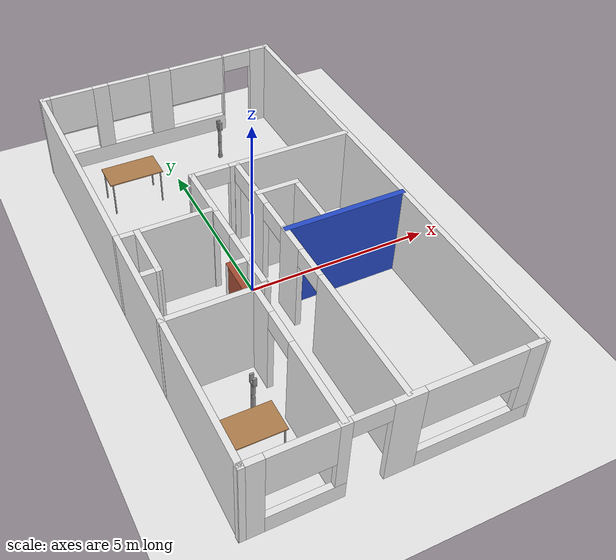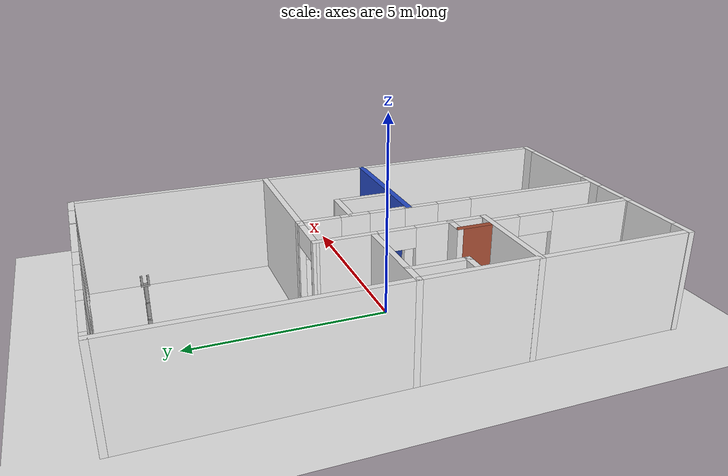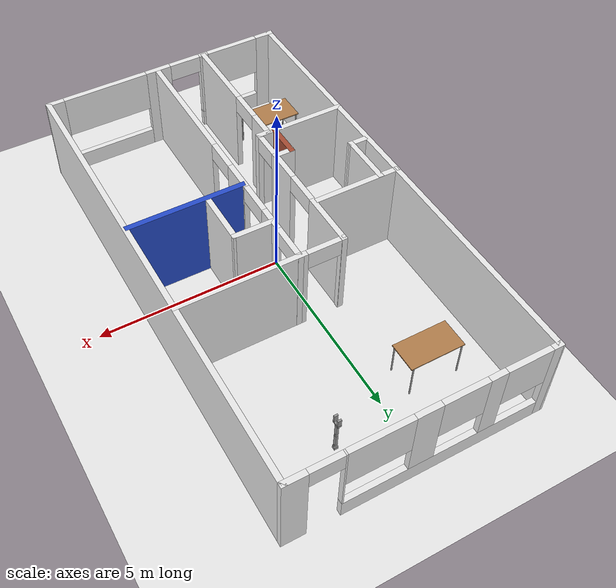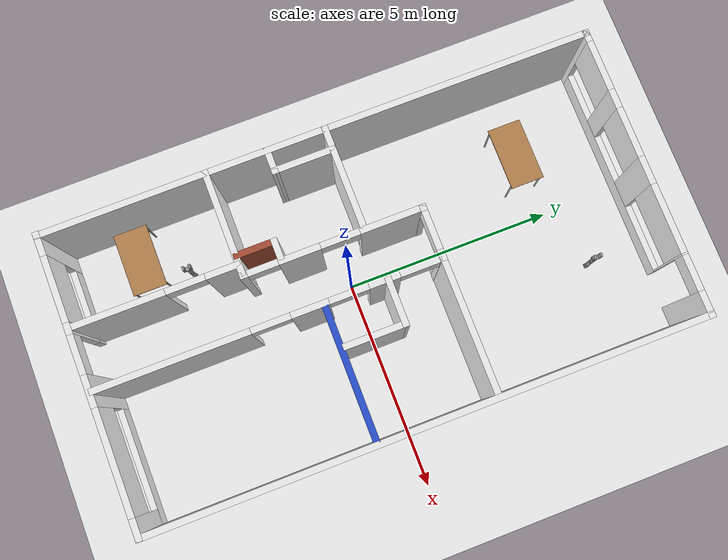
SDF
<sdf version="1.6">
 <world name="default">
  <plugin name="welcome_message" filename="libwelcome_message.so"/>
  <light name="sun" type="directional">
   <pose>0 0 10 0 -0 0</pose>
   <diffuse>0.8 0.8 0.8 1</diffuse>
   <specular>0.2 0.2 0.2 1</specular>
   <attenuation>
    <range>1000</range>
    <constant>0.9</constant>
    <linear>0.01</linear>
    <quadratic>0.001</quadratic>
   </attenuation>
   <direction>-0.5 0.1 -0.9</direction>
  </light>
  <model name="ground_plane">
   <static>1</static>
   <link name="link">
    <collision name="collision">
     <geometry><plane><normal>0 0 1</normal><size>100 100</size></plane></geometry>
     <surface>
      <contact><collide_bitmask>65535</collide_bitmask></contact>
      <friction><ode><mu>100</mu><mu2>50</mu2></ode></friction>
     </surface>
    </collision>
    <visual name="visual">
     <cast_shadows>0</cast_shadows>
     <geometry><plane><normal>0 0 1</normal><size>100 100</size></plane></geometry>
     <material>
      <script><uri>file://media/materials/scripts/gazebo.material</uri><name>Gazebo/White</name></script>
     </material>
    </visual>
   </link>
  </model>
  <gravity>0 0 -9.8</gravity>
  <magnetic_field>6e-06 2.3e-05 -4.2e-05</magnetic_field>
  <atmosphere type="adiabatic"/>
  <physics name="default_physics" default="0" type="ode">
   <max_step_size>0.001</max_step_size>
   <real_time_factor>1</real_time_factor>
   <real_time_update_rate>1000</real_time_update_rate>
  </physics>
  <scene><ambient>0.4 0.4 0.4 1</ambient><background>0.7 0.7 0.7 1</background><shadows>1</shadows></scene>
  <audio><device>default</device></audio>
  <spherical_coordinates>
   <surface_model>EARTH_WGS84</surface_model>
   <latitude_deg>0</latitude_deg>
   <longitude_deg>0</longitude_deg>
   <elevation>0</elevation>
   <heading_deg>0</heading_deg>
  </spherical_coordinates>
  <model name="myapartment">
   <pose>0.279592 0.405357 0 0 -0 0</pose>
   <link name="Wall_0">
    <pose>0.004026 6.44086 0 0 -0 0</pose>
    <visual name="Wall_0_Visual_0">
     <pose>-3.32899 0 1.25 0 -0 0</pose>
     <geometry><box><size>0.289947 0.15 2.5</size></box></geometry>
     <material>
      <script><uri>file://media/materials/scripts/gazebo.material</uri><name>Gazebo/White</name></script>
      <ambient>1 1 1 1</ambient>
     </material>
     <meta><layer>0</layer></meta>
    </visual>
    <collision name="Wall_0_Collision_0">
     <geometry><box><size>0.289947 0.15 2.5</size></box></geometry>
     <pose>-3.32899 0 1.25 0 -0 0</pose>
    </collision>
    <visual name="Wall_0_Visual_1">
     <pose>3.1619 0 1.25 0 -0 0</pose>
     <geometry><box><size>0.624124 0.15 2.5</size></box></geometry>
     <material>
      <script><uri>file://media/materials/scripts/gazebo.material</uri><name>Gazebo/White</name></script>
      <ambient>1 1 1 1</ambient>
     </material>
     <meta><layer>0</layer></meta>
    </visual>
    <collision name="Wall_0_Collision_1">
     <geometry><box><size>0.624124 0.15 2.5</size></box></geometry>
     <pose>3.1619 0 1.25 0 -0 0</pose>
    </collision>
    <visual name="Wall_0_Visual_2">
     <pose>-0.589588 0 0.25 0 -0 0</pose>
     <geometry><box><size>5.18885 0.15 0.5</size></box></geometry>
     <material>
      <script><uri>file://media/materials/scripts/gazebo.material</uri><name>Gazebo/White</name></script>
      <ambient>1 1 1 1</ambient>
     </material>
     <meta><layer>0</layer></meta>
    </visual>
    <collision name="Wall_0_Collision_2">
     <geometry><box><size>5.18885 0.15 0.5</size></box></geometry>
     <pose>-0.589588 0 0.25 0 -0 0</pose>
    </collision>
    <visual name="Wall_0_Visual_3">
     <pose>-1.75147 0 1.5 0 -0 0</pose>
     <geometry><box><size>0.453064 0.15 2</size></box></geometry>
     <material>
      <script><uri>file://media/materials/scripts/gazebo.material</uri><name>Gazebo/White</name></script>
      <ambient>1 1 1 1</ambient>
     </material>
     <meta><layer>0</layer></meta>
    </visual>
    <collision name="Wall_0_Collision_3">
     <geometry><box><size>0.453064 0.15 2</size></box></geometry>
     <pose>-1.75147 0 1.5 0 -0 0</pose>
    </collision>
    <visual name="Wall_0_Visual_4">
     <pose>-0.00315 0 1.5 0 -0 0</pose>
     <geometry><box><size>0.661624 0.15 2</size></box></geometry>
     <material>
      <script><uri>file://media/materials/scripts/gazebo.material</uri><name>Gazebo/White</name></script>
      <ambient>1 1 1 1</ambient>
     </material>
     <meta><layer>0</layer></meta>
    </visual>
    <collision name="Wall_0_Collision_4">
     <geometry><box><size>0.661624 0.15 2</size></box></geometry>
     <pose>-0.00315 0 1.5 0 -0 0</pose>
    </collision>
    <visual name="Wall_0_Visual_5">
     <pose>1.98354 0 1.5 0 -0 0</pose>
     <geometry><box><size>0.042595 0.15 2</size></box></geometry>
     <material>
      <script><uri>file://media/materials/scripts/gazebo.material</uri><name>Gazebo/White</name></script>
      <ambient>1 1 1 1</ambient>
     </material>
     <meta><layer>0</layer></meta>
    </visual>
    <collision name="Wall_0_Collision_5">
     <geometry><box><size>0.042595 0.15 2</size></box></geometry>
     <pose>1.98354 0 1.5 0 -0 0</pose>
    </collision>
    <visual name="Wall_0_Visual_6">
     <pose>-2.58101 0 1.9 0 -0 0</pose>
     <geometry><box><size>1.20601 0.15 1.2</size></box></geometry>
     <material>
      <script><uri>file://media/materials/scripts/gazebo.material</uri><name>Gazebo/White</name></script>
      <ambient>1 1 1 1</ambient>
     </material>
     <meta><layer>0</layer></meta>
    </visual>
    <collision name="Wall_0_Collision_6">
     <geometry><box><size>1.20601 0.15 1.2</size></box></geometry>
     <pose>-2.58101 0 1.9 0 -0 0</pose>
    </collision>
    <visual name="Wall_0_Visual_7">
     <pose>-0.92945 0 1.9 0 -0 0</pose>
     <geometry><box><size>1.19097 0.15 1.2</size></box></geometry>
     <material>
      <script><uri>file://media/materials/scripts/gazebo.material</uri><name>Gazebo/White</name></script>
      <ambient>1 1 1 1</ambient>
     </material>
     <meta><layer>0</layer></meta>
    </visual>
    <collision name="Wall_0_Collision_7">
     <geometry><box><size>1.19097 0.15 1.2</size></box></geometry>
     <pose>-0.92945 0 1.9 0 -0 0</pose>
    </collision>
    <visual name="Wall_0_Visual_8">
     <pose>1.14495 0 1.9 0 -0 0</pose>
     <geometry><box><size>1.63458 0.15 1.2</size></box></geometry>
     <material>
      <script><uri>file://media/materials/scripts/gazebo.material</uri><name>Gazebo/White</name></script>
      <ambient>1 1 1 1</ambient>
     </material>
     <meta><layer>0</layer></meta>
    </visual>
    <collision name="Wall_0_Collision_8">
     <geometry><box><size>1.63458 0.15 1.2</size></box></geometry>
     <pose>1.14495 0 1.9 0 -0 0</pose>
    </collision>
    <visual name="Wall_0_Visual_9">
     <pose>2.42734 0 2.25 0 -0 0</pose>
     <geometry><box><size>0.845 0.15 0.5</size></box></geometry>
     <material>
      <script><uri>file://media/materials/scripts/gazebo.material</uri><name>Gazebo/White</name></script>
      <ambient>1 1 1 1</ambient>
     </material>
     <meta><layer>0</layer></meta>
    </visual>
    <collision name="Wall_0_Collision_9">
     <geometry><box><size>0.845 0.15 0.5</size></box></geometry>
     <pose>2.42734 0 2.25 0 -0 0</pose>
    </collision>
   </link>
   <link name="Wall_11">
    <pose>0.212101 -2.39403 0 0 -0 -1.5708</pose>
    <visual name="Wall_11_Visual_0">
     <pose>-3.96072 0 1.25 0 -0 0</pose>
     <geometry><box><size>0.163567 0.15 2.5</size></box></geometry>
     <material>
      <script><uri>file://media/materials/scripts/gazebo.material</uri><name>Gazebo/White</name></script>
      <ambient>1 1 1 1</ambient>
     </material>
     <meta><layer>0</layer></meta>
    </visual>
    <collision name="Wall_11_Collision_0">
     <geometry><box><size>0.163567 0.15 2.5</size></box></geometry>
     <pose>-3.96072 0 1.25 0 -0 0</pose>
    </collision>
    <visual name="Wall_11_Visual_1">
     <pose>-2.60981 0 1.25 0 -0 0</pose>
     <geometry><box><size>0.718238 0.15 2.5</size></box></geometry>
     <material>
      <script><uri>file://media/materials/scripts/gazebo.material</uri><name>Gazebo/White</name></script>
      <ambient>1 1 1 1</ambient>
     </material>
     <meta><layer>0</layer></meta>
    </visual>
    <collision name="Wall_11_Collision_1">
     <geometry><box><size>0.718238 0.15 2.5</size></box></geometry>
     <pose>-2.60981 0 1.25 0 -0 0</pose>
    </collision>
    <visual name="Wall_11_Visual_2">
     <pose>-0.904498 0 1.25 0 -0 0</pose>
     <geometry><box><size>0.872395 0.15 2.5</size></box></geometry>
     <material>
      <script><uri>file://media/materials/scripts/gazebo.material</uri><name>Gazebo/White</name></script>
      <ambient>1 1 1 1</ambient>
     </material>
     <meta><layer>0</layer></meta>
    </visual>
    <collision name="Wall_11_Collision_2">
     <geometry><box><size>0.872395 0.15 2.5</size></box></geometry>
     <pose>-0.904498 0 1.25 0 -0 0</pose>
    </collision>
    <visual name="Wall_11_Visual_3">
     <pose>2.2421 0 1.25 0 -0 0</pose>
     <geometry><box><size>3.6008 0.15 2.5</size></box></geometry>
     <material>
      <script><uri>file://media/materials/scripts/gazebo.material</uri><name>Gazebo/White</name></script>
      <ambient>1 1 1 1</ambient>
     </material>
     <meta><layer>0</layer></meta>
    </visual>
    <collision name="Wall_11_Collision_3">
     <geometry><box><size>3.6008 0.15 2.5</size></box></geometry>
     <pose>2.2421 0 1.25 0 -0 0</pose>
    </collision>
    <visual name="Wall_11_Visual_4">
     <pose>-3.42393 0 2.25 0 -0 0</pose>
     <geometry><box><size>0.91 0.15 0.5</size></box></geometry>
     <material>
      <script><uri>file://media/materials/scripts/gazebo.material</uri><name>Gazebo/White</name></script>
      <ambient>1 1 1 1</ambient>
     </material>
     <meta><layer>0</layer></meta>
    </visual>
    <collision name="Wall_11_Collision_4">
     <geometry><box><size>0.91 0.15 0.5</size></box></geometry>
     <pose>-3.42393 0 2.25 0 -0 0</pose>
    </collision>
    <visual name="Wall_11_Visual_5">
     <pose>-1.7957 0 2.25 0 -0 0</pose>
     <geometry><box><size>0.91 0.15 0.5</size></box></geometry>
     <material>
      <script><uri>file://media/materials/scripts/gazebo.material</uri><name>Gazebo/White</name></script>
      <ambient>1 1 1 1</ambient>
     </material>
     <meta><layer>0</layer></meta>
    </visual>
    <collision name="Wall_11_Collision_5">
     <geometry><box><size>0.91 0.15 0.5</size></box></geometry>
     <pose>-1.7957 0 2.25 0 -0 0</pose>
    </collision>
    <visual name="Wall_11_Visual_6">
     <pose>-0.0133 0 2.25 0 -0 0</pose>
     <geometry><box><size>0.91 0.15 0.5</size></box></geometry>
     <material>
      <script><uri>file://media/materials/scripts/gazebo.material</uri><name>Gazebo/White</name></script>
      <ambient>1 1 1 1</ambient>
     </material>
     <meta><layer>0</layer></meta>
    </visual>
    <collision name="Wall_11_Collision_6">
     <geometry><box><size>0.91 0.15 0.5</size></box></geometry>
     <pose>-0.0133 0 2.25 0 -0 0</pose>
    </collision>
   </link>
   <link name="Wall_13">
    <collision name="Wall_13_Collision">
     <geometry><box><size>3.25 0.15 2.5</size></box></geometry>
     <pose>0 0 1.25 0 -0 0</pose>
    </collision>
    <visual name="Wall_13_Visual">
     <pose>0 0 1.25 0 -0 0</pose>
     <geometry><box><size>3.25 0.15 2.5</size></box></geometry>
     <material>
      <script><uri>file://media/materials/scripts/gazebo.material</uri><name>Gazebo/Blue</name></script>
      <ambient>1 1 1 1</ambient>
     </material>
     <meta><layer>0</layer></meta>
    </visual>
    <pose>1.79413 -1.1673 0 0 -0 0</pose>
   </link>
   <link name="Wall_15">
    <collision name="Wall_15_Collision">
     <geometry><box><size>2.57057 0.15 2.5</size></box></geometry>
     <pose>0 0 1.25 0 -0 0</pose>
    </collision>
    <visual name="Wall_15_Visual">
     <pose>0 0 1.25 0 -0 0</pose>
     <geometry><box><size>2.57057 0.15 2.5</size></box></geometry>
     <material>
      <script><uri>file://media/materials/scripts/gazebo.material</uri><name>Gazebo/White</name></script>
      <ambient>1 1 1 1</ambient>
     </material>
     <meta><layer>0</layer></meta>
    </visual>
    <pose>-2.18397 -2.58264 0 0 -0 0.001239</pose>
   </link>
   <link name="Wall_16">
    <pose>-0.976474 -0.504642 0 0 -0 1.57224</pose>
    <visual name="Wall_16_Visual_0">
     <pose>-2.06696 0 1.25 0 -0 0</pose>
     <geometry><box><size>0.16959 0.15 2.5</size></box></geometry>
     <material>
      <script><uri>file://media/materials/scripts/gazebo.material</uri><name>Gazebo/White</name></script>
      <ambient>1 1 1 1</ambient>
     </material>
     <meta><layer>0</layer></meta>
    </visual>
    <collision name="Wall_16_Collision_0">
     <geometry><box><size>0.16959 0.15 2.5</size></box></geometry>
     <pose>-2.06696 0 1.25 0 -0 0</pose>
    </collision>
    <visual name="Wall_16_Visual_1">
     <pose>-0.787342 0 1.25 0 -0 0</pose>
     <geometry><box><size>0.969649 0.15 2.5</size></box></geometry>
     <material>
      <script><uri>file://media/materials/scripts/gazebo.material</uri><name>Gazebo/White</name></script>
      <ambient>1 1 1 1</ambient>
     </material>
     <meta><layer>0</layer></meta>
    </visual>
    <collision name="Wall_16_Collision_1">
     <geometry><box><size>0.969649 0.15 2.5</size></box></geometry>
     <pose>-0.787342 0 1.25 0 -0 0</pose>
    </collision>
    <visual name="Wall_16_Visual_2">
     <pose>1.37962 0 1.25 0 -0 0</pose>
     <geometry><box><size>1.54427 0.15 2.5</size></box></geometry>
     <material>
      <script><uri>file://media/materials/scripts/gazebo.material</uri><name>Gazebo/White</name></script>
      <ambient>1 1 1 1</ambient>
     </material>
     <meta><layer>0</layer></meta>
    </visual>
    <collision name="Wall_16_Collision_2">
     <geometry><box><size>1.54427 0.15 2.5</size></box></geometry>
     <pose>1.37962 0 1.25 0 -0 0</pose>
    </collision>
    <visual name="Wall_16_Visual_3">
     <pose>-1.62717 0 2.25 0 -0 0</pose>
     <geometry><box><size>0.71 0.15 0.5</size></box></geometry>
     <material>
      <script><uri>file://media/materials/scripts/gazebo.material</uri><name>Gazebo/White</name></script>
      <ambient>1 1 1 1</ambient>
     </material>
     <meta><layer>0</layer></meta>
    </visual>
    <collision name="Wall_16_Collision_3">
     <geometry><box><size>0.71 0.15 0.5</size></box></geometry>
     <pose>-1.62717 0 2.25 0 -0 0</pose>
    </collision>
    <visual name="Wall_16_Visual_4">
     <pose>0.152483 0 2.25 0 -0 0</pose>
     <geometry><box><size>0.91 0.15 0.5</size></box></geometry>
     <material>
      <script><uri>file://media/materials/scripts/gazebo.material</uri><name>Gazebo/White</name></script>
      <ambient>1 1 1 1</ambient>
     </material>
     <meta><layer>0</layer></meta>
    </visual>
    <collision name="Wall_16_Collision_4">
     <geometry><box><size>0.91 0.15 0.5</size></box></geometry>
     <pose>0.152483 0 2.25 0 -0 0</pose>
    </collision>
   </link>
   <link name="Wall_2">
    <collision name="Wall_2_Collision">
     <geometry><box><size>2.44429 0.15 2.5</size></box></geometry>
     <pose>0 0 1.25 0 -0 0</pose>
    </collision>
    <visual name="Wall_2_Visual">
     <pose>0 0 1.25 0 -0 0</pose>
     <geometry><box><size>2.44429 0.15 2.5</size></box></geometry>
     <material>
      <script><uri>file://media/materials/scripts/gazebo.material</uri><name>Gazebo/White</name></script>
      <ambient>1 1 1 1</ambient>
     </material>
     <meta><layer>0</layer></meta>
    </visual>
    <pose>-2.24753 0.21226 0 0 -0 0.001223</pose>
   </link>
   <link name="Wall_20">
    <collision name="Wall_20_Collision">
     <geometry><box><size>1.16648 0.15 2.5</size></box></geometry>
     <pose>0 0 1.25 0 -0 0</pose>
    </collision>
    <visual name="Wall_20_Visual">
     <pose>0 0 1.25 0 -0 0</pose>
     <geometry><box><size>1.16648 0.15 2.5</size></box></geometry>
     <material>
      <script><uri>file://media/materials/scripts/gazebo.material</uri><name>Gazebo/White</name></script>
      <ambient>1 1 1 1</ambient>
     </material>
     <meta><layer>0</layer></meta>
    </visual>
    <pose>0.733441 0.29699 0 0 -0 -0.003108</pose>
   </link>
   <link name="Wall_21">
    <collision name="Wall_21_Collision">
     <geometry><box><size>1.5 0.15 2.5</size></box></geometry>
     <pose>0 0 1.25 0 -0 0</pose>
    </collision>
    <visual name="Wall_21_Visual">
     <pose>0 0 1.25 0 -0 0</pose>
     <geometry><box><size>1.5 0.15 2.5</size></box></geometry>
     <material>
      <script><uri>file://media/materials/scripts/gazebo.material</uri><name>Gazebo/White</name></script>
      <ambient>1 1 1 1</ambient>
     </material>
     <meta><layer>0</layer></meta>
    </visual>
    <pose>1.24163 -0.379589 0 0 -0 -1.5708</pose>
   </link>
   <link name="Wall_23">
    <collision name="Wall_23_Collision">
     <geometry><box><size>0.627823 0.15 2.5</size></box></geometry>
     <pose>0 0 1.25 0 -0 0</pose>
    </collision>
    <visual name="Wall_23_Visual">
     <pose>0 0 1.25 0 -0 0</pose>
     <geometry><box><size>0.627823 0.15 2.5</size></box></geometry>
     <material>
      <script><uri>file://media/materials/scripts/gazebo.material</uri><name>Gazebo/White</name></script>
      <ambient>1 1 1 1</ambient>
     </material>
     <meta><layer>0</layer></meta>
    </visual>
    <pose>-3.14109 -1.14756 0 0 -0 -0.002313</pose>
   </link>
   <link name="Wall_24">
    <collision name="Wall_24_Collision">
     <geometry><box><size>1.5 0.15 2.5</size></box></geometry>
     <pose>0 0 1.25 0 -0 0</pose>
    </collision>
    <visual name="Wall_24_Visual">
     <pose>0 0 1.25 0 -0 0</pose>
     <geometry><box><size>1.5 0.15 2.5</size></box></geometry>
     <material>
      <script><uri>file://media/materials/scripts/gazebo.material</uri><name>Gazebo/White</name></script>
      <ambient>1 1 1 1</ambient>
     </material>
     <meta><layer>0</layer></meta>
    </visual>
    <pose>-2.90218 -0.473117 0 0 -0 1.5708</pose>
   </link>
   <link name="Wall_26">
    <collision name="Wall_26_Collision">
     <geometry><box><size>1.01076 0.15 2.5</size></box></geometry>
     <pose>0 0 1.25 0 -0 0</pose>
    </collision>
    <visual name="Wall_26_Visual">
     <pose>0 0 1.25 0 -0 0</pose>
     <geometry><box><size>1.01076 0.15 2.5</size></box></geometry>
     <material>
      <script><uri>file://media/materials/scripts/gazebo.material</uri><name>Gazebo/Bricks</name></script>
      <ambient>0.333333 0.666667 1 1</ambient>
     </material>
     <meta><layer>0</layer></meta>
    </visual>
    <pose>-1.42759 -2.12454 0 0 -0 1.5708</pose>
   </link>
   <link name="Wall_27">
    <collision name="Wall_27_Collision">
     <geometry><box><size>0.597111 0.15 2.5</size></box></geometry>
     <pose>0 0 1.25 0 -0 0</pose>
    </collision>
    <visual name="Wall_27_Visual">
     <pose>0 0 1.25 0 -0 0</pose>
     <geometry><box><size>0.597111 0.15 2.5</size></box></geometry>
     <material>
      <script><uri>file://media/materials/scripts/gazebo.material</uri><name>Gazebo/White</name></script>
      <ambient>1 1 1 1</ambient>
     </material>
     <meta><layer>0</layer></meta>
    </visual>
    <pose>-1.20404 -1.69387 0 0 -0 0</pose>
   </link>
   <link name="Wall_30">
    <pose>-1.23247 -4.50024 0 0 -0 1.5708</pose>
    <visual name="Wall_30_Visual_0">
     <pose>-0.859688 0 1.25 0 -0 0</pose>
     <geometry><box><size>2.20454 0.15 2.5</size></box></geometry>
     <material>
      <script><uri>file://media/materials/scripts/gazebo.material</uri><name>Gazebo/White</name></script>
      <ambient>1 1 1 1</ambient>
     </material>
     <meta><layer>0</layer></meta>
    </visual>
    <collision name="Wall_30_Collision_0">
     <geometry><box><size>2.20454 0.15 2.5</size></box></geometry>
     <pose>-0.859688 0 1.25 0 -0 0</pose>
    </collision>
    <visual name="Wall_30_Visual_1">
     <pose>1.55727 0 1.25 0 -0 0</pose>
     <geometry><box><size>0.809377 0.15 2.5</size></box></geometry>
     <material>
      <script><uri>file://media/materials/scripts/gazebo.material</uri><name>Gazebo/White</name></script>
      <ambient>1 1 1 1</ambient>
     </material>
     <meta><layer>0</layer></meta>
    </visual>
    <collision name="Wall_30_Collision_1">
     <geometry><box><size>0.809377 0.15 2.5</size></box></geometry>
     <pose>1.55727 0 1.25 0 -0 0</pose>
    </collision>
    <visual name="Wall_30_Visual_2">
     <pose>0.69758 0 2.25 0 -0 0</pose>
     <geometry><box><size>0.91 0.15 0.5</size></box></geometry>
     <material>
      <script><uri>file://media/materials/scripts/gazebo.material</uri><name>Gazebo/White</name></script>
      <ambient>1 1 1 1</ambient>
     </material>
     <meta><layer>0</layer></meta>
    </visual>
    <collision name="Wall_30_Collision_2">
     <geometry><box><size>0.91 0.15 0.5</size></box></geometry>
     <pose>0.69758 0 2.25 0 -0 0</pose>
    </collision>
   </link>
   <link name="Wall_4">
    <pose>1.20903 1.56986 0 0 -0 -0.000914</pose>
    <visual name="Wall_4_Visual_0">
     <pose>-2.18431 0 1.25 0 -0 0</pose>
     <geometry><box><size>0.158379 0.15 2.5</size></box></geometry>
     <material>
      <script><uri>file://media/materials/scripts/gazebo.material</uri><name>Gazebo/White</name></script>
      <ambient>1 1 1 1</ambient>
     </material>
     <meta><layer>0</layer></meta>
    </visual>
    <collision name="Wall_4_Collision_0">
     <geometry><box><size>0.158379 0.15 2.5</size></box></geometry>
     <pose>-2.18431 0 1.25 0 -0 0</pose>
    </collision>
    <visual name="Wall_4_Visual_1">
     <pose>0.53419 0 1.25 0 -0 0</pose>
     <geometry><box><size>3.45862 0.15 2.5</size></box></geometry>
     <material>
      <script><uri>file://media/materials/scripts/gazebo.material</uri><name>Gazebo/White</name></script>
      <ambient>1 1 1 1</ambient>
     </material>
     <meta><layer>0</layer></meta>
    </visual>
    <collision name="Wall_4_Collision_1">
     <geometry><box><size>3.45862 0.15 2.5</size></box></geometry>
     <pose>0.53419 0 1.25 0 -0 0</pose>
    </collision>
    <visual name="Wall_4_Visual_2">
     <pose>-1.65012 0 2.25 0 -0 0</pose>
     <geometry><box><size>0.91 0.15 0.5</size></box></geometry>
     <material>
      <script><uri>file://media/materials/scripts/gazebo.material</uri><name>Gazebo/White</name></script>
      <ambient>1 1 1 1</ambient>
     </material>
     <meta><layer>0</layer></meta>
    </visual>
    <collision name="Wall_4_Collision_2">
     <geometry><box><size>0.91 0.15 0.5</size></box></geometry>
     <pose>-1.65012 0 2.25 0 -0 0</pose>
    </collision>
   </link>
   <link name="Wall_6">
    <collision name="Wall_6_Collision">
     <geometry><box><size>6.38 0.15 2.5</size></box></geometry>
     <pose>0 0 1.25 0 -0 0</pose>
    </collision>
    <visual name="Wall_6_Visual">
     <pose>0 0 1.25 0 -0 0</pose>
     <geometry><box><size>6.38 0.15 2.5</size></box></geometry>
     <material>
      <script><uri>file://media/materials/scripts/gazebo.material</uri><name>Gazebo/White</name></script>
      <ambient>1 1 1 1</ambient>
     </material>
     <meta><layer>0</layer></meta>
    </visual>
    <pose>-3.39447 3.32586 0 0 -0 -1.5708</pose>
   </link>
   <link name="Wall_7">
    <collision name="Wall_7_Collision">
     <geometry><box><size>6.80168 0.15 2.5</size></box></geometry>
     <pose>0 0 1.25 0 -0 0</pose>
    </collision>
    <visual name="Wall_7_Visual">
     <pose>0 0 1.25 0 -0 0</pose>
     <geometry><box><size>6.80168 0.15 2.5</size></box></geometry>
     <material>
      <script><uri>file://media/materials/scripts/gazebo.material</uri><name>Gazebo/White</name></script>
      <ambient>1 1 1 1</ambient>
     </material>
     <meta><layer>0</layer></meta>
    </visual>
    <pose>-3.39 -3.11487 0 0 -0 -1.56945</pose>
   </link>
   <link name="Wall_8">
    <pose>-9.6e-05 -6.42837 0 0 -0 0.003593</pose>
    <visual name="Wall_8_Visual_0">
     <pose>-3.19294 0 1.25 0 -0 0</pose>
     <geometry><box><size>0.569398 0.15 2.5</size></box></geometry>
     <material>
      <script><uri>file://media/materials/scripts/gazebo.material</uri><name>Gazebo/White</name></script>
      <ambient>1 1 1 1</ambient>
     </material>
     <meta><layer>0</layer></meta>
    </visual>
    <collision name="Wall_8_Collision_0">
     <geometry><box><size>0.569398 0.15 2.5</size></box></geometry>
     <pose>-3.19294 0 1.25 0 -0 0</pose>
    </collision>
    <visual name="Wall_8_Visual_1">
     <pose>0.189812 0 1.25 0 -0 0</pose>
     <geometry><box><size>0.738405 0.15 2.5</size></box></geometry>
     <material>
      <script><uri>file://media/materials/scripts/gazebo.material</uri><name>Gazebo/White</name></script>
      <ambient>1 1 1 1</ambient>
     </material>
     <meta><layer>0</layer></meta>
    </visual>
    <collision name="Wall_8_Collision_1">
     <geometry><box><size>0.738405 0.15 2.5</size></box></geometry>
     <pose>0.189812 0 1.25 0 -0 0</pose>
    </collision>
    <visual name="Wall_8_Visual_2">
     <pose>-1.99882 0 0.25 0 -0 0</pose>
     <geometry><box><size>1.81886 0.15 0.5</size></box></geometry>
     <material>
      <script><uri>file://media/materials/scripts/gazebo.material</uri><name>Gazebo/White</name></script>
      <ambient>1 1 1 1</ambient>
     </material>
     <meta><layer>0</layer></meta>
    </visual>
    <collision name="Wall_8_Collision_2">
     <geometry><box><size>1.81886 0.15 0.5</size></box></geometry>
     <pose>-1.99882 0 0.25 0 -0 0</pose>
    </collision>
    <visual name="Wall_8_Visual_3">
     <pose>2.01833 0 0.25 0 -0 0</pose>
     <geometry><box><size>2.91863 0.15 0.5</size></box></geometry>
     <material>
      <script><uri>file://media/materials/scripts/gazebo.material</uri><name>Gazebo/White</name></script>
      <ambient>1 1 1 1</ambient>
     </material>
     <meta><layer>0</layer></meta>
    </visual>
    <collision name="Wall_8_Collision_3">
     <geometry><box><size>2.91863 0.15 0.5</size></box></geometry>
     <pose>2.01833 0 0.25 0 -0 0</pose>
    </collision>
    <visual name="Wall_8_Visual_4">
     <pose>-1.22615 0 1.5 0 -0 0</pose>
     <geometry><box><size>0.27352 0.15 2</size></box></geometry>
     <material>
      <script><uri>file://media/materials/scripts/gazebo.material</uri><name>Gazebo/White</name></script>
      <ambient>1 1 1 1</ambient>
     </material>
     <meta><layer>0</layer></meta>
    </visual>
    <collision name="Wall_8_Collision_4">
     <geometry><box><size>0.27352 0.15 2</size></box></geometry>
     <pose>-1.22615 0 1.5 0 -0 0</pose>
    </collision>
    <visual name="Wall_8_Visual_5">
     <pose>-1.22615 0 1.5 0 -0 0</pose>
     <geometry><box><size>0.27352 0.15 2</size></box></geometry>
     <material>
      <script><uri>file://media/materials/scripts/gazebo.material</uri><name>Gazebo/White</name></script>
      <ambient>1 1 1 1</ambient>
     </material>
     <meta><layer>0</layer></meta>
    </visual>
    <collision name="Wall_8_Collision_5">
     <geometry><box><size>0.27352 0.15 2</size></box></geometry>
     <pose>-1.22615 0 1.5 0 -0 0</pose>
    </collision>
    <visual name="Wall_8_Visual_6">
     <pose>3.22578 0 1.5 0 -0 0</pose>
     <geometry><box><size>0.503738 0.15 2</size></box></geometry>
     <material>
      <script><uri>file://media/materials/scripts/gazebo.material</uri><name>Gazebo/White</name></script>
      <ambient>1 1 1 1</ambient>
     </material>
     <meta><layer>0</layer></meta>
    </visual>
    <collision name="Wall_8_Collision_6">
     <geometry><box><size>0.503738 0.15 2</size></box></geometry>
     <pose>3.22578 0 1.5 0 -0 0</pose>
    </collision>
    <visual name="Wall_8_Visual_7">
     <pose>-2.13558 0 1.9 0 -0 0</pose>
     <geometry><box><size>1.54534 0.15 1.2</size></box></geometry>
     <material>
      <script><uri>file://media/materials/scripts/gazebo.material</uri><name>Gazebo/White</name></script>
      <ambient>1 1 1 1</ambient>
     </material>
     <meta><layer>0</layer></meta>
    </visual>
    <collision name="Wall_8_Collision_7">
     <geometry><box><size>1.54534 0.15 1.2</size></box></geometry>
     <pose>-2.13558 0 1.9 0 -0 0</pose>
    </collision>
    <visual name="Wall_8_Visual_8">
     <pose>1.76646 0 1.9 0 -0 0</pose>
     <geometry><box><size>2.41489 0.15 1.2</size></box></geometry>
     <material>
      <script><uri>file://media/materials/scripts/gazebo.material</uri><name>Gazebo/White</name></script>
      <ambient>1 1 1 1</ambient>
     </material>
     <meta><layer>0</layer></meta>
    </visual>
    <collision name="Wall_8_Collision_8">
     <geometry><box><size>2.41489 0.15 1.2</size></box></geometry>
     <pose>1.76646 0 1.9 0 -0 0</pose>
    </collision>
    <visual name="Wall_8_Visual_9">
     <pose>-0.634391 0 2.25 0 -0 0</pose>
     <geometry><box><size>0.91 0.15 0.5</size></box></geometry>
     <material>
      <script><uri>file://media/materials/scripts/gazebo.material</uri><name>Gazebo/White</name></script>
      <ambient>1 1 1 1</ambient>
     </material>
     <meta><layer>0</layer></meta>
    </visual>
    <collision name="Wall_8_Collision_9">
     <geometry><box><size>0.91 0.15 0.5</size></box></geometry>
     <pose>-0.634391 0 2.25 0 -0 0</pose>
    </collision>
    <visual name="Wall_8_Visual_10">
     <pose>-0.634391 0 2.25 0 -0 0</pose>
     <geometry><box><size>0.91 0.15 0.5</size></box></geometry>
     <material>
      <script><uri>file://media/materials/scripts/gazebo.material</uri><name>Gazebo/White</name></script>
      <ambient>1 1 1 1</ambient>
     </material>
     <meta><layer>0</layer></meta>
    </visual>
    <collision name="Wall_8_Collision_10">
     <geometry><box><size>0.91 0.15 0.5</size></box></geometry>
     <pose>-0.634391 0 2.25 0 -0 0</pose>
    </collision>
   </link>
   <link name="Wall_9">
    <collision name="Wall_9_Collision">
     <geometry><box><size>13.007 0.15 2.5</size></box></geometry>
     <pose>0 0 1.25 0 -0 0</pose>
    </collision>
    <visual name="Wall_9_Visual">
     <pose>0 0 1.25 0 -0 0</pose>
     <geometry><box><size>13.007 0.15 2.5</size></box></geometry>
     <material>
      <script><uri>file://media/materials/scripts/gazebo.material</uri><name>Gazebo/White</name></script>
      <ambient>1 1 1 1</ambient>
     </material>
     <meta><layer>0</layer></meta>
    </visual>
    <pose>3.40253 0.012358 0 0 -0 1.5708</pose>
   </link>
   <static>1</static>
  </model>
  <model name="table">
   <static>1</static>
   <link name="link">
    <collision name="surface">
     <pose>0 0 1 0 -0 0</pose>
     <geometry><box><size>1.5 0.8 0.03</size></box></geometry>
     <surface><friction><ode><mu>0.6</mu><mu2>0.6</mu2></ode></friction></surface>
    </collision>
    <visual name="visual1">
     <pose>0 0 1 0 -0 0</pose>
     <geometry><box><size>1.5 0.8 0.03</size></box></geometry>
     <material>
      <script><uri>file://media/materials/scripts/gazebo.material</uri><name>Gazebo/Wood</name></script>
     </material>
    </visual>
    <collision name="front_left_leg">
     <pose>0.68 0.38 0.5 0 -0 0</pose>
     <geometry><cylinder><radius>0.02</radius><length>1</length></cylinder></geometry>
    </collision>
    <visual name="front_left_leg">
     <pose>0.68 0.38 0.5 0 -0 0</pose>
     <geometry><cylinder><radius>0.02</radius><length>1</length></cylinder></geometry>
     <material>
      <script><uri>file://media/materials/scripts/gazebo.material</uri><name>Gazebo/Grey</name></script>
     </material>
    </visual>
    <collision name="front_right_leg">
     <pose>0.68 -0.38 0.5 0 -0 0</pose>
     <geometry><cylinder><radius>0.02</radius><length>1</length></cylinder></geometry>
    </collision>
    <visual name="front_right_leg">
     <pose>0.68 -0.38 0.5 0 -0 0</pose>
     <geometry><cylinder><radius>0.02</radius><length>1</length></cylinder></geometry>
     <material>
      <script><uri>file://media/materials/scripts/gazebo.material</uri><name>Gazebo/Grey</name></script>
     </material>
    </visual>
    <collision name="back_right_leg">
     <pose>-0.68 -0.38 0.5 0 -0 0</pose>
     <geometry><cylinder><radius>0.02</radius><length>1</length></cylinder></geometry>
    </collision>
    <visual name="back_right_leg">
     <pose>-0.68 -0.38 0.5 0 -0 0</pose>
     <geometry><cylinder><radius>0.02</radius><length>1</length></cylinder></geometry>
     <material>
      <script><uri>file://media/materials/scripts/gazebo.material</uri><name>Gazebo/Grey</name></script>
     </material>
    </visual>
    <collision name="back_left_leg">
     <pose>-0.68 0.38 0.5 0 -0 0</pose>
     <geometry><cylinder><radius>0.02</radius><length>1</length></cylinder></geometry>
    </collision>
    <visual name="back_left_leg">
     <pose>-0.68 0.38 0.5 0 -0 0</pose>
     <geometry><cylinder><radius>0.02</radius><length>1</length></cylinder></geometry>
     <material>
      <script><uri>file://media/materials/scripts/gazebo.material</uri><name>Gazebo/Grey</name></script>
     </material>
    </visual>
   </link>
   <pose>-1.42953 4.69698 0 0 -0 0</pose>
  </model>
  <model name="myrobotarm_clone">
   <link name="Base">
    <inertial>
     <mass>1</mass>
     <inertia>
      <ixx>0.166667</ixx>
      <ixy>0</ixy>
      <ixz>0</ixz>
      <iyy>0.166667</iyy>
      <iyz>0</iyz>
      <izz>0.166667</izz>
     </inertia>
    </inertial>
    <pose>1.29977 -2.48919 -0.073664 0 -0 0</pose>
    <visual name="visual">
     <geometry><box><size>0.1 0.1 0.1</size></box></geometry>
     <material>
      <lighting>1</lighting>
      <script><uri>file://media/materials/scripts/gazebo.material</uri><name>Gazebo/Grey</name></script>
      <shader type="pixel"><normal_map>__default__</normal_map></shader>
      <ambient>0.3 0.3 0.3 1</ambient>
      <diffuse>0.7 0.7 0.7 1</diffuse>
      <specular>0.01 0.01 0.01 1</specular>
      <emissive>0 0 0 1</emissive>
     </material>
    </visual>
    <collision name="collision">
     <geometry><box><size>0.1 0.1 0.1</size></box></geometry>
     <surface>
      <friction>
       <ode><mu>1</mu><mu2>1</mu2><fdir1>0 0 0</fdir1><slip1>0</slip1><slip2>0</slip2></ode>
       <torsional>
        <coefficient>1</coefficient>
        <patch_radius>0</patch_radius>
        <surface_radius>0</surface_radius>
        <use_patch_radius>1</use_patch_radius>
        <ode><slip>0</slip></ode>
       </torsional>
      </friction>
      <bounce><restitution_coefficient>0</restitution_coefficient><threshold>1e+06</threshold></bounce>
      <contact>
       <collide_without_contact>0</collide_without_contact>
       <collide_without_contact_bitmask>1</collide_without_contact_bitmask>
       <collide_bitmask>1</collide_bitmask>
       <ode>
        <soft_cfm>0</soft_cfm>
        <soft_erp>0.2</soft_erp>
        <kp>1e+13</kp>
        <kd>1</kd>
        <max_vel>0.01</max_vel>
        <min_depth>0</min_depth>
       </ode>
       <bullet>
        <split_impulse>1</split_impulse>
        <split_impulse_penetration_threshold>-0.01</split_impulse_penetration_threshold>
        <soft_cfm>0</soft_cfm>
        <soft_erp>0.2</soft_erp>
        <kp>1e+13</kp>
        <kd>1</kd>
       </bullet>
      </contact>
     </surface>
    </collision>
   </link>
   <link name="Base_hinge">
    <inertial>
     <mass>1</mass>
     <inertia><ixx>0.1</ixx><ixy>0</ixy><ixz>0</ixz><iyy>0.1</iyy><iyz>0</iyz><izz>0.1</izz></inertia>
    </inertial>
    <pose>1.29977 -2.48919 0.026336 0 -0 0</pose>
    <visual name="visual">
     <geometry><sphere><radius>0.05</radius></sphere></geometry>
     <material>
      <lighting>1</lighting>
      <script><uri>file://media/materials/scripts/gazebo.material</uri><name>Gazebo/Grey</name></script>
      <shader type="pixel"><normal_map>__default__</normal_map></shader>
      <ambient>0.3 0.3 0.3 1</ambient>
      <diffuse>0.7 0.7 0.7 1</diffuse>
      <specular>0.01 0.01 0.01 1</specular>
      <emissive>0 0 0 1</emissive>
     </material>
    </visual>
    <collision name="collision">
     <geometry><sphere><radius>0.05</radius></sphere></geometry>
     <surface>
      <friction>
       <ode><mu>1</mu><mu2>1</mu2><fdir1>0 0 0</fdir1><slip1>0</slip1><slip2>0</slip2></ode>
       <torsional>
        <coefficient>1</coefficient>
        <patch_radius>0</patch_radius>
        <surface_radius>0</surface_radius>
        <use_patch_radius>1</use_patch_radius>
        <ode><slip>0</slip></ode>
       </torsional>
      </friction>
      <bounce><restitution_coefficient>0</restitution_coefficient><threshold>1e+06</threshold></bounce>
      <contact>
       <collide_without_contact>0</collide_without_contact>
       <collide_without_contact_bitmask>1</collide_without_contact_bitmask>
       <collide_bitmask>1</collide_bitmask>
       <ode>
        <soft_cfm>0</soft_cfm>
        <soft_erp>0.2</soft_erp>
        <kp>1e+13</kp>
        <kd>1</kd>
        <max_vel>0.01</max_vel>
        <min_depth>0</min_depth>
       </ode>
       <bullet>
        <split_impulse>1</split_impulse>
        <split_impulse_penetration_threshold>-0.01</split_impulse_penetration_threshold>
        <soft_cfm>0</soft_cfm>
        <soft_erp>0.2</soft_erp>
        <kp>1e+13</kp>
        <kd>1</kd>
       </bullet>
      </contact>
     </surface>
    </collision>
   </link>
   <link name="Gripper_base">
    <inertial>
     <mass>1</mass>
     <inertia>
      <ixx>0.166667</ixx>
      <ixy>0</ixy>
      <ixz>0</ixz>
      <iyy>0.166667</iyy>
      <iyz>0</iyz>
      <izz>0.166667</izz>
     </inertia>
    </inertial>
    <pose>1.29977 -2.48919 0.901336 0 -0 0</pose>
    <visual name="visual">
     <geometry><box><size>0.1 0.2 0.05</size></box></geometry>
     <material>
      <lighting>1</lighting>
      <script><uri>file://media/materials/scripts/gazebo.material</uri><name>Gazebo/Grey</name></script>
      <shader type="vertex"><normal_map>__default__</normal_map></shader>
      <ambient>0.3 0.3 0.3 1</ambient>
      <diffuse>0.7 0.7 0.7 1</diffuse>
      <specular>0.01 0.01 0.01 1</specular>
      <emissive>0 0 0 1</emissive>
     </material>
    </visual>
    <collision name="collision">
     <geometry><box><size>0.1 0.2 0.05</size></box></geometry>
     <surface>
      <friction>
       <ode><mu>1</mu><mu2>1</mu2><fdir1>0 0 0</fdir1><slip1>0</slip1><slip2>0</slip2></ode>
       <torsional>
        <coefficient>1</coefficient>
        <patch_radius>0</patch_radius>
        <surface_radius>0</surface_radius>
        <use_patch_radius>1</use_patch_radius>
        <ode><slip>0</slip></ode>
       </torsional>
      </friction>
      <bounce><restitution_coefficient>0</restitution_coefficient><threshold>1e+06</threshold></bounce>
      <contact>
       <collide_without_contact>0</collide_without_contact>
       <collide_without_contact_bitmask>1</collide_without_contact_bitmask>
       <collide_bitmask>1</collide_bitmask>
       <ode>
        <soft_cfm>0</soft_cfm>
        <soft_erp>0.2</soft_erp>
        <kp>1e+13</kp>
        <kd>1</kd>
        <max_vel>0.01</max_vel>
        <min_depth>0</min_depth>
       </ode>
       <bullet>
        <split_impulse>1</split_impulse>
        <split_impulse_penetration_threshold>-0.01</split_impulse_penetration_threshold>
        <soft_cfm>0</soft_cfm>
        <soft_erp>0.2</soft_erp>
        <kp>1e+13</kp>
        <kd>1</kd>
       </bullet>
      </contact>
     </surface>
    </collision>
   </link>
   <link name="Gripper_left">
    <inertial>
     <mass>1</mass>
     <inertia>
      <ixx>0.166667</ixx>
      <ixy>0</ixy>
      <ixz>0</ixz>
      <iyy>0.166667</iyy>
      <iyz>0</iyz>
      <izz>0.166667</izz>
     </inertia>
    </inertial>
    <pose>1.29977 -2.41418 1.02633 -1.5707 0 0</pose>
    <visual name="visual_0">
     <geometry><box><size>0.1 0.2 0.05</size></box></geometry>
     <material>
      <lighting>1</lighting>
      <script><uri>file://media/materials/scripts/gazebo.material</uri><name>Gazebo/Grey</name></script>
      <shader type="vertex"><normal_map>__default__</normal_map></shader>
      <ambient>0.3 0.3 0.3 1</ambient>
      <diffuse>0.7 0.7 0.7 1</diffuse>
      <specular>0.01 0.01 0.01 1</specular>
      <emissive>0 0 0 1</emissive>
     </material>
    </visual>
    <collision name="collision">
     <geometry><box><size>0.1 0.2 0.05</size></box></geometry>
     <surface>
      <friction>
       <ode><mu>1</mu><mu2>1</mu2><fdir1>0 0 0</fdir1><slip1>0</slip1><slip2>0</slip2></ode>
       <torsional>
        <coefficient>1</coefficient>
        <patch_radius>0</patch_radius>
        <surface_radius>0</surface_radius>
        <use_patch_radius>1</use_patch_radius>
        <ode><slip>0</slip></ode>
       </torsional>
      </friction>
      <bounce><restitution_coefficient>0</restitution_coefficient><threshold>1e+06</threshold></bounce>
      <contact>
       <collide_without_contact>0</collide_without_contact>
       <collide_without_contact_bitmask>1</collide_without_contact_bitmask>
       <collide_bitmask>1</collide_bitmask>
       <ode>
        <soft_cfm>0</soft_cfm>
        <soft_erp>0.2</soft_erp>
        <kp>1e+13</kp>
        <kd>1</kd>
        <max_vel>0.01</max_vel>
        <min_depth>0</min_depth>
       </ode>
       <bullet>
        <split_impulse>1</split_impulse>
        <split_impulse_penetration_threshold>-0.01</split_impulse_penetration_threshold>
        <soft_cfm>0</soft_cfm>
        <soft_erp>0.2</soft_erp>
        <kp>1e+13</kp>
        <kd>1</kd>
       </bullet>
      </contact>
     </surface>
    </collision>
   </link>
   <link name="Gripper_right">
    <inertial>
     <mass>1</mass>
     <inertia>
      <ixx>0.166667</ixx>
      <ixy>0</ixy>
      <ixz>0</ixz>
      <iyy>0.166667</iyy>
      <iyz>0</iyz>
      <izz>0.166667</izz>
     </inertia>
    </inertial>
    <pose>1.29977 -2.56418 1.02633 1.5707 -0 0</pose>
    <visual name="visual_0">
     <geometry><box><size>0.1 0.2 0.05</size></box></geometry>
     <material>
      <lighting>1</lighting>
      <script><uri>file://media/materials/scripts/gazebo.material</uri><name>Gazebo/Grey</name></script>
      <shader type="vertex"><normal_map>__default__</normal_map></shader>
      <ambient>0.3 0.3 0.3 1</ambient>
      <diffuse>0.7 0.7 0.7 1</diffuse>
      <specular>0.01 0.01 0.01 1</specular>
      <emissive>0 0 0 1</emissive>
     </material>
    </visual>
    <collision name="collision">
     <geometry><box><size>0.1 0.2 0.05</size></box></geometry>
     <surface>
      <friction>
       <ode><mu>1</mu><mu2>1</mu2><fdir1>0 0 0</fdir1><slip1>0</slip1><slip2>0</slip2></ode>
       <torsional>
        <coefficient>1</coefficient>
        <patch_radius>0</patch_radius>
        <surface_radius>0</surface_radius>
        <use_patch_radius>1</use_patch_radius>
        <ode><slip>0</slip></ode>
       </torsional>
      </friction>
      <bounce><restitution_coefficient>0</restitution_coefficient><threshold>1e+06</threshold></bounce>
      <contact>
       <collide_without_contact>0</collide_without_contact>
       <collide_without_contact_bitmask>1</collide_without_contact_bitmask>
       <collide_bitmask>1</collide_bitmask>
       <ode>
        <soft_cfm>0</soft_cfm>
        <soft_erp>0.2</soft_erp>
        <kp>1e+13</kp>
        <kd>1</kd>
        <max_vel>0.01</max_vel>
        <min_depth>0</min_depth>
       </ode>
       <bullet>
        <split_impulse>1</split_impulse>
        <split_impulse_penetration_threshold>-0.01</split_impulse_penetration_threshold>
        <soft_cfm>0</soft_cfm>
        <soft_erp>0.2</soft_erp>
        <kp>1e+13</kp>
        <kd>1</kd>
       </bullet>
      </contact>
     </surface>
    </collision>
   </link>
   <link name="Section1">
    <inertial>
     <mass>1</mass>
     <inertia><ixx>0.145833</ixx><ixy>0</ixy><ixz>0</ixz><iyy>0.145833</iyy><iyz>0</iyz><izz>0.125</izz></inertia>
    </inertial>
    <pose>1.29977 -2.48919 0.251336 0 -0 0</pose>
    <visual name="visual">
     <geometry><cylinder><radius>0.05</radius><length>0.35</length></cylinder></geometry>
     <material>
      <lighting>1</lighting>
      <script><uri>file://media/materials/scripts/gazebo.material</uri><name>Gazebo/Grey</name></script>
      <shader type="pixel"><normal_map>__default__</normal_map></shader>
      <ambient>0.3 0.3 0.3 1</ambient>
      <diffuse>0.7 0.7 0.7 1</diffuse>
      <specular>0.01 0.01 0.01 1</specular>
      <emissive>0 0 0 1</emissive>
     </material>
    </visual>
    <collision name="collision">
     <geometry><cylinder><radius>0.05</radius><length>0.35</length></cylinder></geometry>
     <surface>
      <friction>
       <ode><mu>1</mu><mu2>1</mu2><fdir1>0 0 0</fdir1><slip1>0</slip1><slip2>0</slip2></ode>
       <torsional>
        <coefficient>1</coefficient>
        <patch_radius>0</patch_radius>
        <surface_radius>0</surface_radius>
        <use_patch_radius>1</use_patch_radius>
        <ode><slip>0</slip></ode>
       </torsional>
      </friction>
      <bounce><restitution_coefficient>0</restitution_coefficient><threshold>1e+06</threshold></bounce>
      <contact>
       <collide_without_contact>0</collide_without_contact>
       <collide_without_contact_bitmask>1</collide_without_contact_bitmask>
       <collide_bitmask>1</collide_bitmask>
       <ode>
        <soft_cfm>0</soft_cfm>
        <soft_erp>0.2</soft_erp>
        <kp>1e+13</kp>
        <kd>1</kd>
        <max_vel>0.01</max_vel>
        <min_depth>0</min_depth>
       </ode>
       <bullet>
        <split_impulse>1</split_impulse>
        <split_impulse_penetration_threshold>-0.01</split_impulse_penetration_threshold>
        <soft_cfm>0</soft_cfm>
        <soft_erp>0.2</soft_erp>
        <kp>1e+13</kp>
        <kd>1</kd>
       </bullet>
      </contact>
     </surface>
    </collision>
   </link>
   <link name="Section1_hinge">
    <inertial>
     <mass>1</mass>
     <inertia><ixx>0.1</ixx><ixy>0</ixy><ixz>0</ixz><iyy>0.1</iyy><iyz>0</iyz><izz>0.1</izz></inertia>
    </inertial>
    <pose>1.29977 -2.48919 0.476336 0 -0 0</pose>
    <visual name="visual">
     <geometry><sphere><radius>0.05</radius></sphere></geometry>
     <material>
      <lighting>1</lighting>
      <script><uri>file://media/materials/scripts/gazebo.material</uri><name>Gazebo/Grey</name></script>
      <shader type="pixel"><normal_map>__default__</normal_map></shader>
      <ambient>0.3 0.3 0.3 1</ambient>
      <diffuse>0.7 0.7 0.7 1</diffuse>
      <specular>0.01 0.01 0.01 1</specular>
      <emissive>0 0 0 1</emissive>
     </material>
    </visual>
    <collision name="collision">
     <geometry><sphere><radius>0.05</radius></sphere></geometry>
     <surface>
      <friction>
       <ode><mu>1</mu><mu2>1</mu2><fdir1>0 0 0</fdir1><slip1>0</slip1><slip2>0</slip2></ode>
       <torsional>
        <coefficient>1</coefficient>
        <patch_radius>0</patch_radius>
        <surface_radius>0</surface_radius>
        <use_patch_radius>1</use_patch_radius>
        <ode><slip>0</slip></ode>
       </torsional>
      </friction>
      <bounce><restitution_coefficient>0</restitution_coefficient><threshold>1e+06</threshold></bounce>
      <contact>
       <collide_without_contact>0</collide_without_contact>
       <collide_without_contact_bitmask>1</collide_without_contact_bitmask>
       <collide_bitmask>1</collide_bitmask>
       <ode>
        <soft_cfm>0</soft_cfm>
        <soft_erp>0.2</soft_erp>
        <kp>1e+13</kp>
        <kd>1</kd>
        <max_vel>0.01</max_vel>
        <min_depth>0</min_depth>
       </ode>
       <bullet>
        <split_impulse>1</split_impulse>
        <split_impulse_penetration_threshold>-0.01</split_impulse_penetration_threshold>
        <soft_cfm>0</soft_cfm>
        <soft_erp>0.2</soft_erp>
        <kp>1e+13</kp>
        <kd>1</kd>
       </bullet>
      </contact>
     </surface>
    </collision>
   </link>
   <link name="Section2">
    <inertial>
     <mass>1</mass>
     <inertia><ixx>0.145833</ixx><ixy>0</ixy><ixz>0</ixz><iyy>0.145833</iyy><iyz>0</iyz><izz>0.125</izz></inertia>
    </inertial>
    <pose>1.29977 -2.48919 0.701336 0 -0 0</pose>
    <visual name="visual">
     <geometry><cylinder><radius>0.05</radius><length>0.35</length></cylinder></geometry>
     <material>
      <lighting>1</lighting>
      <script><uri>file://media/materials/scripts/gazebo.material</uri><name>Gazebo/Grey</name></script>
      <shader type="pixel"><normal_map>__default__</normal_map></shader>
      <ambient>0.3 0.3 0.3 1</ambient>
      <diffuse>0.7 0.7 0.7 1</diffuse>
      <specular>0.01 0.01 0.01 1</specular>
      <emissive>0 0 0 1</emissive>
     </material>
    </visual>
    <collision name="collision">
     <geometry><cylinder><radius>0.05</radius><length>0.35</length></cylinder></geometry>
     <surface>
      <friction>
       <ode><mu>1</mu><mu2>1</mu2><fdir1>0 0 0</fdir1><slip1>0</slip1><slip2>0</slip2></ode>
       <torsional>
        <coefficient>1</coefficient>
        <patch_radius>0</patch_radius>
        <surface_radius>0</surface_radius>
        <use_patch_radius>1</use_patch_radius>
        <ode><slip>0</slip></ode>
       </torsional>
      </friction>
      <bounce><restitution_coefficient>0</restitution_coefficient><threshold>1e+06</threshold></bounce>
      <contact>
       <collide_without_contact>0</collide_without_contact>
       <collide_without_contact_bitmask>1</collide_without_contact_bitmask>
       <collide_bitmask>1</collide_bitmask>
       <ode>
        <soft_cfm>0</soft_cfm>
        <soft_erp>0.2</soft_erp>
        <kp>1e+13</kp>
        <kd>1</kd>
        <max_vel>0.01</max_vel>
        <min_depth>0</min_depth>
       </ode>
       <bullet>
        <split_impulse>1</split_impulse>
        <split_impulse_penetration_threshold>-0.01</split_impulse_penetration_threshold>
        <soft_cfm>0</soft_cfm>
        <soft_erp>0.2</soft_erp>
        <kp>1e+13</kp>
        <kd>1</kd>
       </bullet>
      </contact>
     </surface>
    </collision>
   </link>
   <joint name="Fix1" type="fixed">
    <parent>Section1</parent>
    <child>Section1_hinge</child>
    <physics>
     <ode><limit><cfm>0</cfm><erp>0.2</erp></limit><suspension><cfm>0</cfm><erp>0.2</erp></suspension></ode>
    </physics>
   </joint>
   <joint name="Gripper_J_left" type="prismatic">
    <parent>Gripper_base</parent>
    <child>Gripper_right</child>
    <axis>
     <xyz>0 0 1</xyz>
     <use_parent_model_frame>0</use_parent_model_frame>
     <limit>
      <lower>-1.79769e+308</lower>
      <upper>1.79769e+308</upper>
      <effort>-1</effort>
      <velocity>-1</velocity>
     </limit>
     <dynamics>
      <spring_reference>0</spring_reference>
      <spring_stiffness>0</spring_stiffness>
      <damping>0</damping>
      <friction>3</friction>
     </dynamics>
    </axis>
    <physics>
     <ode><limit><cfm>0</cfm><erp>0.2</erp></limit><suspension><cfm>0</cfm><erp>0.2</erp></suspension></ode>
    </physics>
   </joint>
   <joint name="Gripper_J_right" type="prismatic">
    <parent>Gripper_base</parent>
    <child>Gripper_left</child>
    <axis>
     <xyz>0 0 1</xyz>
     <use_parent_model_frame>0</use_parent_model_frame>
     <limit>
      <lower>-1.79769e+308</lower>
      <upper>1.79769e+308</upper>
      <effort>-1</effort>
      <velocity>-1</velocity>
     </limit>
     <dynamics>
      <spring_reference>0</spring_reference>
      <spring_stiffness>0</spring_stiffness>
      <damping>0</damping>
      <friction>3</friction>
     </dynamics>
    </axis>
    <physics>
     <ode><limit><cfm>0</cfm><erp>0.2</erp></limit><suspension><cfm>0</cfm><erp>0.2</erp></suspension></ode>
    </physics>
   </joint>
   <joint name="J1" type="revolute">
    <parent>Base</parent>
    <child>Base_hinge</child>
    <axis>
     <xyz>0 0 1</xyz>
     <use_parent_model_frame>0</use_parent_model_frame>
     <limit>
      <lower>-1.79769e+308</lower>
      <upper>1.79769e+308</upper>
      <effort>-1</effort>
      <velocity>-1</velocity>
     </limit>
     <dynamics>
      <spring_reference>0</spring_reference>
      <spring_stiffness>0</spring_stiffness>
      <damping>0</damping>
      <friction>3</friction>
     </dynamics>
    </axis>
    <physics>
     <ode><limit><cfm>0</cfm><erp>0.2</erp></limit><suspension><cfm>0</cfm><erp>0.2</erp></suspension></ode>
    </physics>
   </joint>
   <joint name="J2" type="revolute">
    <parent>Section1</parent>
    <child>Base_hinge</child>
    <axis>
     <xyz>0 1 0</xyz>
     <use_parent_model_frame>0</use_parent_model_frame>
     <limit>
      <lower>-1.79769e+308</lower>
      <upper>1.79769e+308</upper>
      <effort>-1</effort>
      <velocity>-1</velocity>
     </limit>
     <dynamics>
      <spring_reference>0</spring_reference>
      <spring_stiffness>0</spring_stiffness>
      <damping>0</damping>
      <friction>3</friction>
     </dynamics>
    </axis>
    <physics>
     <ode><limit><cfm>0</cfm><erp>0.2</erp></limit><suspension><cfm>0</cfm><erp>0.2</erp></suspension></ode>
    </physics>
   </joint>
   <joint name="J3" type="revolute">
    <parent>Section2</parent>
    <child>Section1_hinge</child>
    <axis>
     <xyz>0 1 0</xyz>
     <use_parent_model_frame>0</use_parent_model_frame>
     <limit>
      <lower>-1.79769e+308</lower>
      <upper>1.79769e+308</upper>
      <effort>-1</effort>
      <velocity>-1</velocity>
     </limit>
     <dynamics>
      <spring_reference>0</spring_reference>
      <spring_stiffness>0</spring_stiffness>
      <damping>0</damping>
      <friction>3</friction>
     </dynamics>
    </axis>
    <physics>
     <ode><limit><cfm>0</cfm><erp>0.2</erp></limit><suspension><cfm>0</cfm><erp>0.2</erp></suspension></ode>
    </physics>
   </joint>
   <joint name="J4" type="revolute">
    <parent>Gripper_base</parent>
    <child>Section2</child>
    <axis>
     <xyz>0 0 1</xyz>
     <use_parent_model_frame>0</use_parent_model_frame>
     <limit>
      <lower>-1.79769e+308</lower>
      <upper>1.79769e+308</upper>
      <effort>-1</effort>
      <velocity>-1</velocity>
     </limit>
     <dynamics>
      <spring_reference>0</spring_reference>
      <spring_stiffness>0</spring_stiffness>
      <damping>0</damping>
      <friction>3</friction>
     </dynamics>
    </axis>
    <physics>
     <ode><limit><cfm>0</cfm><erp>0.2</erp></limit><suspension><cfm>0</cfm><erp>0.2</erp></suspension></ode>
    </physics>
   </joint>
   <static>0</static>
   <pose>-2.89457 -0.918577 0.125753 0.000825 -5e-06 -0.001281</pose>
  </model>
  <model name="table_clone">
   <static>1</static>
   <link name="link">
    <collision name="surface">
     <pose>0 0 1 0 -0 0</pose>
     <geometry><box><size>1.5 0.8 0.03</size></box></geometry>
     <surface><friction><ode><mu>0.6</mu><mu2>0.6</mu2></ode></friction></surface>
    </collision>
    <visual name="visual1">
     <pose>0 0 1 0 -0 0</pose>
     <geometry><box><size>1.5 0.8 0.03</size></box></geometry>
     <material>
      <script><uri>file://media/materials/scripts/gazebo.material</uri><name>Gazebo/Wood</name></script>
     </material>
    </visual>
    <collision name="front_left_leg">
     <pose>0.68 0.38 0.5 0 -0 0</pose>
     <geometry><cylinder><radius>0.02</radius><length>1</length></cylinder></geometry>
    </collision>
    <visual name="front_left_leg">
     <pose>0.68 0.38 0.5 0 -0 0</pose>
     <geometry><cylinder><radius>0.02</radius><length>1</length></cylinder></geometry>
     <material>
      <script><uri>file://media/materials/scripts/gazebo.material</uri><name>Gazebo/Grey</name></script>
     </material>
    </visual>
    <collision name="front_right_leg">
     <pose>0.68 -0.38 0.5 0 -0 0</pose>
     <geometry><cylinder><radius>0.02</radius><length>1</length></cylinder></geometry>
    </collision>
    <visual name="front_right_leg">
     <pose>0.68 -0.38 0.5 0 -0 0</pose>
     <geometry><cylinder><radius>0.02</radius><length>1</length></cylinder></geometry>
     <material>
      <script><uri>file://media/materials/scripts/gazebo.material</uri><name>Gazebo/Grey</name></script>
     </material>
    </visual>
    <collision name="back_right_leg">
     <pose>-0.68 -0.38 0.5 0 -0 0</pose>
     <geometry><cylinder><radius>0.02</radius><length>1</length></cylinder></geometry>
    </collision>
    <visual name="back_right_leg">
     <pose>-0.68 -0.38 0.5 0 -0 0</pose>
     <geometry><cylinder><radius>0.02</radius><length>1</length></cylinder></geometry>
     <material>
      <script><uri>file://media/materials/scripts/gazebo.material</uri><name>Gazebo/Grey</name></script>
     </material>
    </visual>
    <collision name="back_left_leg">
     <pose>-0.68 0.38 0.5 0 -0 0</pose>
     <geometry><cylinder><radius>0.02</radius><length>1</length></cylinder></geometry>
    </collision>
    <visual name="back_left_leg">
     <pose>-0.68 0.38 0.5 0 -0 0</pose>
     <geometry><cylinder><radius>0.02</radius><length>1</length></cylinder></geometry>
     <material>
      <script><uri>file://media/materials/scripts/gazebo.material</uri><name>Gazebo/Grey</name></script>
     </material>
    </visual>
   </link>
   <pose>-2.19041 -4.37801 0 0 -0 0</pose>
  </model>
  <model name="myrobotarm_clone_clone">
   <link name="Base">
    <inertial>
     <mass>1</mass>
     <inertia>
      <ixx>0.166667</ixx>
      <ixy>0</ixy>
      <ixz>0</ixz>
      <iyy>0.166667</iyy>
      <iyz>0</iyz>
      <izz>0.166667</izz>
     </inertia>
    </inertial>
    <pose>1.29977 -2.48919 -0.073664 0 -0 0</pose>
    <visual name="visual">
     <geometry><box><size>0.1 0.1 0.1</size></box></geometry>
     <material>
      <lighting>1</lighting>
      <script><uri>file://media/materials/scripts/gazebo.material</uri><name>Gazebo/Grey</name></script>
      <shader type="pixel"><normal_map>__default__</normal_map></shader>
      <ambient>0.3 0.3 0.3 1</ambient>
      <diffuse>0.7 0.7 0.7 1</diffuse>
      <specular>0.01 0.01 0.01 1</specular>
      <emissive>0 0 0 1</emissive>
     </material>
    </visual>
    <collision name="collision">
     <geometry><box><size>0.1 0.1 0.1</size></box></geometry>
     <surface>
      <friction>
       <ode><mu>1</mu><mu2>1</mu2><fdir1>0 0 0</fdir1><slip1>0</slip1><slip2>0</slip2></ode>
       <torsional>
        <coefficient>1</coefficient>
        <patch_radius>0</patch_radius>
        <surface_radius>0</surface_radius>
        <use_patch_radius>1</use_patch_radius>
        <ode><slip>0</slip></ode>
       </torsional>
      </friction>
      <bounce><restitution_coefficient>0</restitution_coefficient><threshold>1e+06</threshold></bounce>
      <contact>
       <collide_without_contact>0</collide_without_contact>
       <collide_without_contact_bitmask>1</collide_without_contact_bitmask>
       <collide_bitmask>1</collide_bitmask>
       <ode>
        <soft_cfm>0</soft_cfm>
        <soft_erp>0.2</soft_erp>
        <kp>1e+13</kp>
        <kd>1</kd>
        <max_vel>0.01</max_vel>
        <min_depth>0</min_depth>
       </ode>
       <bullet>
        <split_impulse>1</split_impulse>
        <split_impulse_penetration_threshold>-0.01</split_impulse_penetration_threshold>
        <soft_cfm>0</soft_cfm>
        <soft_erp>0.2</soft_erp>
        <kp>1e+13</kp>
        <kd>1</kd>
       </bullet>
      </contact>
     </surface>
    </collision>
   </link>
   <link name="Base_hinge">
    <inertial>
     <mass>1</mass>
     <inertia><ixx>0.1</ixx><ixy>0</ixy><ixz>0</ixz><iyy>0.1</iyy><iyz>0</iyz><izz>0.1</izz></inertia>
    </inertial>
    <pose>1.29977 -2.48919 0.026336 0 -0 0</pose>
    <visual name="visual">
     <geometry><sphere><radius>0.05</radius></sphere></geometry>
     <material>
      <lighting>1</lighting>
      <script><uri>file://media/materials/scripts/gazebo.material</uri><name>Gazebo/Grey</name></script>
      <shader type="pixel"><normal_map>__default__</normal_map></shader>
      <ambient>0.3 0.3 0.3 1</ambient>
      <diffuse>0.7 0.7 0.7 1</diffuse>
      <specular>0.01 0.01 0.01 1</specular>
      <emissive>0 0 0 1</emissive>
     </material>
    </visual>
    <collision name="collision">
     <geometry><sphere><radius>0.05</radius></sphere></geometry>
     <surface>
      <friction>
       <ode><mu>1</mu><mu2>1</mu2><fdir1>0 0 0</fdir1><slip1>0</slip1><slip2>0</slip2></ode>
       <torsional>
        <coefficient>1</coefficient>
        <patch_radius>0</patch_radius>
        <surface_radius>0</surface_radius>
        <use_patch_radius>1</use_patch_radius>
        <ode><slip>0</slip></ode>
       </torsional>
      </friction>
      <bounce><restitution_coefficient>0</restitution_coefficient><threshold>1e+06</threshold></bounce>
      <contact>
       <collide_without_contact>0</collide_without_contact>
       <collide_without_contact_bitmask>1</collide_without_contact_bitmask>
       <collide_bitmask>1</collide_bitmask>
       <ode>
        <soft_cfm>0</soft_cfm>
        <soft_erp>0.2</soft_erp>
        <kp>1e+13</kp>
        <kd>1</kd>
        <max_vel>0.01</max_vel>
        <min_depth>0</min_depth>
       </ode>
       <bullet>
        <split_impulse>1</split_impulse>
        <split_impulse_penetration_threshold>-0.01</split_impulse_penetration_threshold>
        <soft_cfm>0</soft_cfm>
        <soft_erp>0.2</soft_erp>
        <kp>1e+13</kp>
        <kd>1</kd>
       </bullet>
      </contact>
     </surface>
    </collision>
   </link>
   <link name="Gripper_base">
    <inertial>
     <mass>1</mass>
     <inertia>
      <ixx>0.166667</ixx>
      <ixy>0</ixy>
      <ixz>0</ixz>
      <iyy>0.166667</iyy>
      <iyz>0</iyz>
      <izz>0.166667</izz>
     </inertia>
    </inertial>
    <pose>1.29977 -2.48919 0.901336 0 -0 0</pose>
    <visual name="visual">
     <geometry><box><size>0.1 0.2 0.05</size></box></geometry>
     <material>
      <lighting>1</lighting>
      <script><uri>file://media/materials/scripts/gazebo.material</uri><name>Gazebo/Grey</name></script>
      <shader type="vertex"><normal_map>__default__</normal_map></shader>
      <ambient>0.3 0.3 0.3 1</ambient>
      <diffuse>0.7 0.7 0.7 1</diffuse>
      <specular>0.01 0.01 0.01 1</specular>
      <emissive>0 0 0 1</emissive>
     </material>
    </visual>
    <collision name="collision">
     <geometry><box><size>0.1 0.2 0.05</size></box></geometry>
     <surface>
      <friction>
       <ode><mu>1</mu><mu2>1</mu2><fdir1>0 0 0</fdir1><slip1>0</slip1><slip2>0</slip2></ode>
       <torsional>
        <coefficient>1</coefficient>
        <patch_radius>0</patch_radius>
        <surface_radius>0</surface_radius>
        <use_patch_radius>1</use_patch_radius>
        <ode><slip>0</slip></ode>
       </torsional>
      </friction>
      <bounce><restitution_coefficient>0</restitution_coefficient><threshold>1e+06</threshold></bounce>
      <contact>
       <collide_without_contact>0</collide_without_contact>
       <collide_without_contact_bitmask>1</collide_without_contact_bitmask>
       <collide_bitmask>1</collide_bitmask>
       <ode>
        <soft_cfm>0</soft_cfm>
        <soft_erp>0.2</soft_erp>
        <kp>1e+13</kp>
        <kd>1</kd>
        <max_vel>0.01</max_vel>
        <min_depth>0</min_depth>
       </ode>
       <bullet>
        <split_impulse>1</split_impulse>
        <split_impulse_penetration_threshold>-0.01</split_impulse_penetration_threshold>
        <soft_cfm>0</soft_cfm>
        <soft_erp>0.2</soft_erp>
        <kp>1e+13</kp>
        <kd>1</kd>
       </bullet>
      </contact>
     </surface>
    </collision>
   </link>
   <link name="Gripper_left">
    <inertial>
     <mass>1</mass>
     <inertia>
      <ixx>0.166667</ixx>
      <ixy>0</ixy>
      <ixz>0</ixz>
      <iyy>0.166667</iyy>
      <iyz>0</iyz>
      <izz>0.166667</izz>
     </inertia>
    </inertial>
    <pose>1.29977 -2.41418 1.02633 -1.5707 0 0</pose>
    <visual name="visual_0">
     <geometry><box><size>0.1 0.2 0.05</size></box></geometry>
     <material>
      <lighting>1</lighting>
      <script><uri>file://media/materials/scripts/gazebo.material</uri><name>Gazebo/Grey</name></script>
      <shader type="vertex"><normal_map>__default__</normal_map></shader>
      <ambient>0.3 0.3 0.3 1</ambient>
      <diffuse>0.7 0.7 0.7 1</diffuse>
      <specular>0.01 0.01 0.01 1</specular>
      <emissive>0 0 0 1</emissive>
     </material>
    </visual>
    <collision name="collision">
     <geometry><box><size>0.1 0.2 0.05</size></box></geometry>
     <surface>
      <friction>
       <ode><mu>1</mu><mu2>1</mu2><fdir1>0 0 0</fdir1><slip1>0</slip1><slip2>0</slip2></ode>
       <torsional>
        <coefficient>1</coefficient>
        <patch_radius>0</patch_radius>
        <surface_radius>0</surface_radius>
        <use_patch_radius>1</use_patch_radius>
        <ode><slip>0</slip></ode>
       </torsional>
      </friction>
      <bounce><restitution_coefficient>0</restitution_coefficient><threshold>1e+06</threshold></bounce>
      <contact>
       <collide_without_contact>0</collide_without_contact>
       <collide_without_contact_bitmask>1</collide_without_contact_bitmask>
       <collide_bitmask>1</collide_bitmask>
       <ode>
        <soft_cfm>0</soft_cfm>
        <soft_erp>0.2</soft_erp>
        <kp>1e+13</kp>
        <kd>1</kd>
        <max_vel>0.01</max_vel>
        <min_depth>0</min_depth>
       </ode>
       <bullet>
        <split_impulse>1</split_impulse>
        <split_impulse_penetration_threshold>-0.01</split_impulse_penetration_threshold>
        <soft_cfm>0</soft_cfm>
        <soft_erp>0.2</soft_erp>
        <kp>1e+13</kp>
        <kd>1</kd>
       </bullet>
      </contact>
     </surface>
    </collision>
   </link>
   <link name="Gripper_right">
    <inertial>
     <mass>1</mass>
     <inertia>
      <ixx>0.166667</ixx>
      <ixy>0</ixy>
      <ixz>0</ixz>
      <iyy>0.166667</iyy>
      <iyz>0</iyz>
      <izz>0.166667</izz>
     </inertia>
    </inertial>
    <pose>1.29977 -2.56418 1.02633 1.5707 -0 0</pose>
    <visual name="visual_0">
     <geometry><box><size>0.1 0.2 0.05</size></box></geometry>
     <material>
      <lighting>1</lighting>
      <script><uri>file://media/materials/scripts/gazebo.material</uri><name>Gazebo/Grey</name></script>
      <shader type="vertex"><normal_map>__default__</normal_map></shader>
      <ambient>0.3 0.3 0.3 1</ambient>
      <diffuse>0.7 0.7 0.7 1</diffuse>
      <specular>0.01 0.01 0.01 1</specular>
      <emissive>0 0 0 1</emissive>
     </material>
    </visual>
    <collision name="collision">
     <geometry><box><size>0.1 0.2 0.05</size></box></geometry>
     <surface>
      <friction>
       <ode><mu>1</mu><mu2>1</mu2><fdir1>0 0 0</fdir1><slip1>0</slip1><slip2>0</slip2></ode>
       <torsional>
        <coefficient>1</coefficient>
        <patch_radius>0</patch_radius>
        <surface_radius>0</surface_radius>
        <use_patch_radius>1</use_patch_radius>
        <ode><slip>0</slip></ode>
       </torsional>
      </friction>
      <bounce><restitution_coefficient>0</restitution_coefficient><threshold>1e+06</threshold></bounce>
      <contact>
       <collide_without_contact>0</collide_without_contact>
       <collide_without_contact_bitmask>1</collide_without_contact_bitmask>
       <collide_bitmask>1</collide_bitmask>
       <ode>
        <soft_cfm>0</soft_cfm>
        <soft_erp>0.2</soft_erp>
        <kp>1e+13</kp>
        <kd>1</kd>
        <max_vel>0.01</max_vel>
        <min_depth>0</min_depth>
       </ode>
       <bullet>
        <split_impulse>1</split_impulse>
        <split_impulse_penetration_threshold>-0.01</split_impulse_penetration_threshold>
        <soft_cfm>0</soft_cfm>
        <soft_erp>0.2</soft_erp>
        <kp>1e+13</kp>
        <kd>1</kd>
       </bullet>
      </contact>
     </surface>
    </collision>
   </link>
   <link name="Section1">
    <inertial>
     <mass>1</mass>
     <inertia><ixx>0.145833</ixx><ixy>0</ixy><ixz>0</ixz><iyy>0.145833</iyy><iyz>0</iyz><izz>0.125</izz></inertia>
    </inertial>
    <pose>1.29977 -2.48919 0.251336 0 -0 0</pose>
    <visual name="visual">
     <geometry><cylinder><radius>0.05</radius><length>0.35</length></cylinder></geometry>
     <material>
      <lighting>1</lighting>
      <script><uri>file://media/materials/scripts/gazebo.material</uri><name>Gazebo/Grey</name></script>
      <shader type="pixel"><normal_map>__default__</normal_map></shader>
      <ambient>0.3 0.3 0.3 1</ambient>
      <diffuse>0.7 0.7 0.7 1</diffuse>
      <specular>0.01 0.01 0.01 1</specular>
      <emissive>0 0 0 1</emissive>
     </material>
    </visual>
    <collision name="collision">
     <geometry><cylinder><radius>0.05</radius><length>0.35</length></cylinder></geometry>
     <surface>
      <friction>
       <ode><mu>1</mu><mu2>1</mu2><fdir1>0 0 0</fdir1><slip1>0</slip1><slip2>0</slip2></ode>
       <torsional>
        <coefficient>1</coefficient>
        <patch_radius>0</patch_radius>
        <surface_radius>0</surface_radius>
        <use_patch_radius>1</use_patch_radius>
        <ode><slip>0</slip></ode>
       </torsional>
      </friction>
      <bounce><restitution_coefficient>0</restitution_coefficient><threshold>1e+06</threshold></bounce>
      <contact>
       <collide_without_contact>0</collide_without_contact>
       <collide_without_contact_bitmask>1</collide_without_contact_bitmask>
       <collide_bitmask>1</collide_bitmask>
       <ode>
        <soft_cfm>0</soft_cfm>
        <soft_erp>0.2</soft_erp>
        <kp>1e+13</kp>
        <kd>1</kd>
        <max_vel>0.01</max_vel>
        <min_depth>0</min_depth>
       </ode>
       <bullet>
        <split_impulse>1</split_impulse>
        <split_impulse_penetration_threshold>-0.01</split_impulse_penetration_threshold>
        <soft_cfm>0</soft_cfm>
        <soft_erp>0.2</soft_erp>
        <kp>1e+13</kp>
        <kd>1</kd>
       </bullet>
      </contact>
     </surface>
    </collision>
   </link>
   <link name="Section1_hinge">
    <inertial>
     <mass>1</mass>
     <inertia><ixx>0.1</ixx><ixy>0</ixy><ixz>0</ixz><iyy>0.1</iyy><iyz>0</iyz><izz>0.1</izz></inertia>
    </inertial>
    <pose>1.29977 -2.48919 0.476336 0 -0 0</pose>
    <visual name="visual">
     <geometry><sphere><radius>0.05</radius></sphere></geometry>
     <material>
      <lighting>1</lighting>
      <script><uri>file://media/materials/scripts/gazebo.material</uri><name>Gazebo/Grey</name></script>
      <shader type="pixel"><normal_map>__default__</normal_map></shader>
      <ambient>0.3 0.3 0.3 1</ambient>
      <diffuse>0.7 0.7 0.7 1</diffuse>
      <specular>0.01 0.01 0.01 1</specular>
      <emissive>0 0 0 1</emissive>
     </material>
    </visual>
    <collision name="collision">
     <geometry><sphere><radius>0.05</radius></sphere></geometry>
     <surface>
      <friction>
       <ode><mu>1</mu><mu2>1</mu2><fdir1>0 0 0</fdir1><slip1>0</slip1><slip2>0</slip2></ode>
       <torsional>
        <coefficient>1</coefficient>
        <patch_radius>0</patch_radius>
        <surface_radius>0</surface_radius>
        <use_patch_radius>1</use_patch_radius>
        <ode><slip>0</slip></ode>
       </torsional>
      </friction>
      <bounce><restitution_coefficient>0</restitution_coefficient><threshold>1e+06</threshold></bounce>
      <contact>
       <collide_without_contact>0</collide_without_contact>
       <collide_without_contact_bitmask>1</collide_without_contact_bitmask>
       <collide_bitmask>1</collide_bitmask>
       <ode>
        <soft_cfm>0</soft_cfm>
        <soft_erp>0.2</soft_erp>
        <kp>1e+13</kp>
        <kd>1</kd>
        <max_vel>0.01</max_vel>
        <min_depth>0</min_depth>
       </ode>
       <bullet>
        <split_impulse>1</split_impulse>
        <split_impulse_penetration_threshold>-0.01</split_impulse_penetration_threshold>
        <soft_cfm>0</soft_cfm>
        <soft_erp>0.2</soft_erp>
        <kp>1e+13</kp>
        <kd>1</kd>
       </bullet>
      </contact>
     </surface>
    </collision>
   </link>
   <link name="Section2">
    <inertial>
     <mass>1</mass>
     <inertia><ixx>0.145833</ixx><ixy>0</ixy><ixz>0</ixz><iyy>0.145833</iyy><iyz>0</iyz><izz>0.125</izz></inertia>
    </inertial>
    <pose>1.29977 -2.48919 0.701336 0 -0 0</pose>
    <visual name="visual">
     <geometry><cylinder><radius>0.05</radius><length>0.35</length></cylinder></geometry>
     <material>
      <lighting>1</lighting>
      <script><uri>file://media/materials/scripts/gazebo.material</uri><name>Gazebo/Grey</name></script>
      <shader type="pixel"><normal_map>__default__</normal_map></shader>
      <ambient>0.3 0.3 0.3 1</ambient>
      <diffuse>0.7 0.7 0.7 1</diffuse>
      <specular>0.01 0.01 0.01 1</specular>
      <emissive>0 0 0 1</emissive>
     </material>
    </visual>
    <collision name="collision">
     <geometry><cylinder><radius>0.05</radius><length>0.35</length></cylinder></geometry>
     <surface>
      <friction>
       <ode><mu>1</mu><mu2>1</mu2><fdir1>0 0 0</fdir1><slip1>0</slip1><slip2>0</slip2></ode>
       <torsional>
        <coefficient>1</coefficient>
        <patch_radius>0</patch_radius>
        <surface_radius>0</surface_radius>
        <use_patch_radius>1</use_patch_radius>
        <ode><slip>0</slip></ode>
       </torsional>
      </friction>
      <bounce><restitution_coefficient>0</restitution_coefficient><threshold>1e+06</threshold></bounce>
      <contact>
       <collide_without_contact>0</collide_without_contact>
       <collide_without_contact_bitmask>1</collide_without_contact_bitmask>
       <collide_bitmask>1</collide_bitmask>
       <ode>
        <soft_cfm>0</soft_cfm>
        <soft_erp>0.2</soft_erp>
        <kp>1e+13</kp>
        <kd>1</kd>
        <max_vel>0.01</max_vel>
        <min_depth>0</min_depth>
       </ode>
       <bullet>
        <split_impulse>1</split_impulse>
        <split_impulse_penetration_threshold>-0.01</split_impulse_penetration_threshold>
        <soft_cfm>0</soft_cfm>
        <soft_erp>0.2</soft_erp>
        <kp>1e+13</kp>
        <kd>1</kd>
       </bullet>
      </contact>
     </surface>
    </collision>
   </link>
   <joint name="Fix1" type="fixed">
    <parent>Section1</parent>
    <child>Section1_hinge</child>
    <physics>
     <ode><limit><cfm>0</cfm><erp>0.2</erp></limit><suspension><cfm>0</cfm><erp>0.2</erp></suspension></ode>
    </physics>
   </joint>
   <joint name="Gripper_J_left" type="prismatic">
    <parent>Gripper_base</parent>
    <child>Gripper_right</child>
    <axis>
     <xyz>0 0 1</xyz>
     <use_parent_model_frame>0</use_parent_model_frame>
     <limit>
      <lower>-1.79769e+308</lower>
      <upper>1.79769e+308</upper>
      <effort>-1</effort>
      <velocity>-1</velocity>
     </limit>
     <dynamics>
      <spring_reference>0</spring_reference>
      <spring_stiffness>0</spring_stiffness>
      <damping>0</damping>
      <friction>3</friction>
     </dynamics>
    </axis>
    <physics>
     <ode><limit><cfm>0</cfm><erp>0.2</erp></limit><suspension><cfm>0</cfm><erp>0.2</erp></suspension></ode>
    </physics>
   </joint>
   <joint name="Gripper_J_right" type="prismatic">
    <parent>Gripper_base</parent>
    <child>Gripper_left</child>
    <axis>
     <xyz>0 0 1</xyz>
     <use_parent_model_frame>0</use_parent_model_frame>
     <limit>
      <lower>-1.79769e+308</lower>
      <upper>1.79769e+308</upper>
      <effort>-1</effort>
      <velocity>-1</velocity>
     </limit>
     <dynamics>
      <spring_reference>0</spring_reference>
      <spring_stiffness>0</spring_stiffness>
      <damping>0</damping>
      <friction>3</friction>
     </dynamics>
    </axis>
    <physics>
     <ode><limit><cfm>0</cfm><erp>0.2</erp></limit><suspension><cfm>0</cfm><erp>0.2</erp></suspension></ode>
    </physics>
   </joint>
   <joint name="J1" type="revolute">
    <parent>Base</parent>
    <child>Base_hinge</child>
    <axis>
     <xyz>0 0 1</xyz>
     <use_parent_model_frame>0</use_parent_model_frame>
     <limit>
      <lower>-1.79769e+308</lower>
      <upper>1.79769e+308</upper>
      <effort>-1</effort>
      <velocity>-1</velocity>
     </limit>
     <dynamics>
      <spring_reference>0</spring_reference>
      <spring_stiffness>0</spring_stiffness>
      <damping>0</damping>
      <friction>3</friction>
     </dynamics>
    </axis>
    <physics>
     <ode><limit><cfm>0</cfm><erp>0.2</erp></limit><suspension><cfm>0</cfm><erp>0.2</erp></suspension></ode>
    </physics>
   </joint>
   <joint name="J2" type="revolute">
    <parent>Section1</parent>
    <child>Base_hinge</child>
    <axis>
     <xyz>0 1 0</xyz>
     <use_parent_model_frame>0</use_parent_model_frame>
     <limit>
      <lower>-1.79769e+308</lower>
      <upper>1.79769e+308</upper>
      <effort>-1</effort>
      <velocity>-1</velocity>
     </limit>
     <dynamics>
      <spring_reference>0</spring_reference>
      <spring_stiffness>0</spring_stiffness>
      <damping>0</damping>
      <friction>3</friction>
     </dynamics>
    </axis>
    <physics>
     <ode><limit><cfm>0</cfm><erp>0.2</erp></limit><suspension><cfm>0</cfm><erp>0.2</erp></suspension></ode>
    </physics>
   </joint>
   <joint name="J3" type="revolute">
    <parent>Section2</parent>
    <child>Section1_hinge</child>
    <axis>
     <xyz>0 1 0</xyz>
     <use_parent_model_frame>0</use_parent_model_frame>
     <limit>
      <lower>-1.79769e+308</lower>
      <upper>1.79769e+308</upper>
      <effort>-1</effort>
      <velocity>-1</velocity>
     </limit>
     <dynamics>
      <spring_reference>0</spring_reference>
      <spring_stiffness>0</spring_stiffness>
      <damping>0</damping>
      <friction>3</friction>
     </dynamics>
    </axis>
    <physics>
     <ode><limit><cfm>0</cfm><erp>0.2</erp></limit><suspension><cfm>0</cfm><erp>0.2</erp></suspension></ode>
    </physics>
   </joint>
   <joint name="J4" type="revolute">
    <parent>Gripper_base</parent>
    <child>Section2</child>
    <axis>
     <xyz>0 0 1</xyz>
     <use_parent_model_frame>0</use_parent_model_frame>
     <limit>
      <lower>-1.79769e+308</lower>
      <upper>1.79769e+308</upper>
      <effort>-1</effort>
      <velocity>-1</velocity>
     </limit>
     <dynamics>
      <spring_reference>0</spring_reference>
      <spring_stiffness>0</spring_stiffness>
      <damping>0</damping>
      <friction>3</friction>
     </dynamics>
    </axis>
    <physics>
     <ode><limit><cfm>0</cfm><erp>0.2</erp></limit><suspension><cfm>0</cfm><erp>0.2</erp></suspension></ode>
    </physics>
   </joint>
   <static>0</static>
   <pose>0.234309 7.96078 0.12104 -0.001071 -3e-06 0.001329</pose>
  </model>
 </world>
</sdf>
